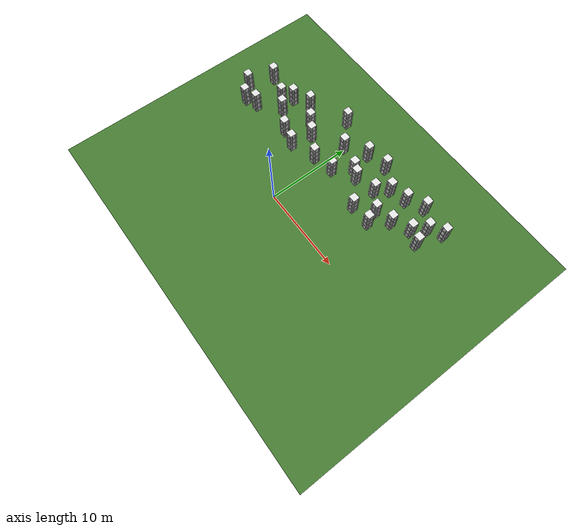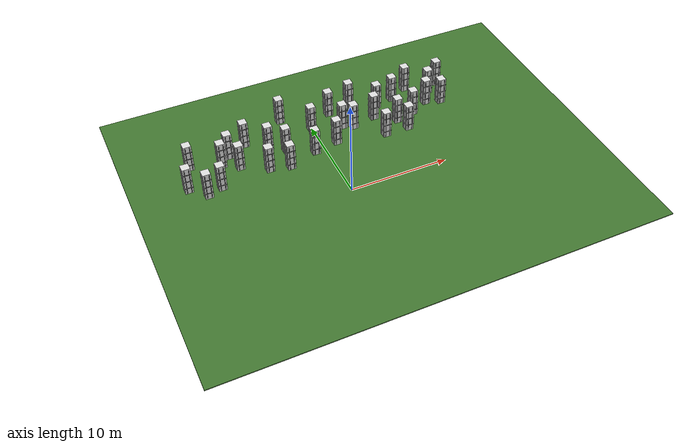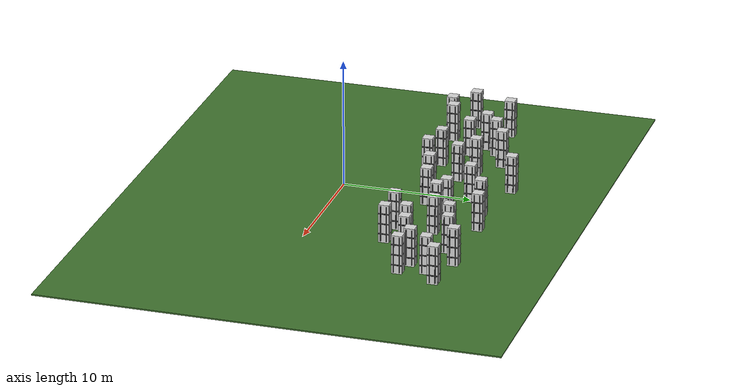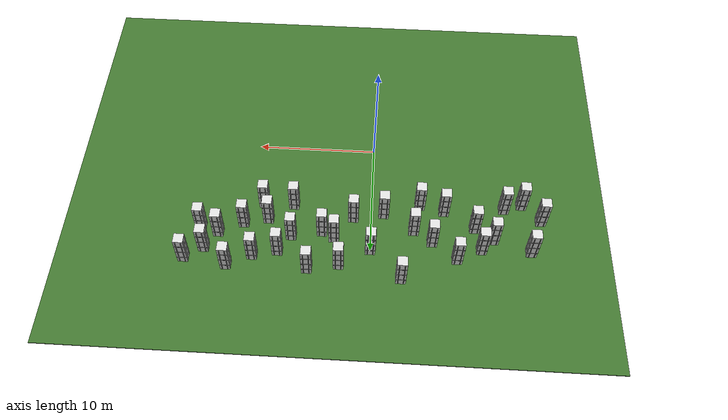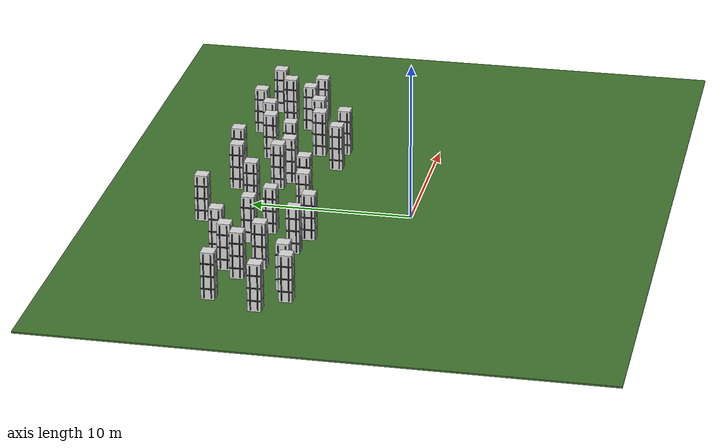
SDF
<?xml version='1.0'?>
<sdf version='1.6'>
  <world name='dense_world_complex'>

    <gui fullscreen='0'>
      <camera name='user_camera'>
        <pose>-49 27 52 0 0.75 -0.76 0</pose>
      </camera>
    </gui>

    <shadows>0</shadows>

    <light name='sun' type='directional'>
      <cast_shadows>1</cast_shadows>
      <pose>0 0 20 0 0 0</pose>
      <diffuse>0.8 0.8 0.8 1</diffuse>
      <specular>0.2 0.2 0.2 1</specular>
      <attenuation>
        <range>1000</range>
        <constant>0.9</constant>
        <linear>0.01</linear>
        <quadratic>0.001</quadratic>
      </attenuation>
      <direction>-0.5 0.1 -0.9</direction>
    </light>

    <physics name='default_physics' default='1' type='ode'>
      <max_step_size>0.005</max_step_size>
      <real_time_factor>1</real_time_factor>
      <real_time_update_rate>200</real_time_update_rate>
    </physics>

    <model name='ground'>
      <static>1</static>
      <link name='link'>
        <collision name='collision'>
          <geometry>
            <box>
              <size>45 35 0.1</size>
            </box>
          </geometry>
        </collision>
        <visual name='visual'>
          <geometry>
            <box>
              <size>45 35 0.1</size>
            </box>
          </geometry>
          <material>
            <ambient>0.25 0.45 0.18 1</ambient>
            <diffuse>0.25 0.45 0.18 1</diffuse>
          </material>
        </visual>
      </link>
      <pose>3 2 -0.05 0 0 0</pose>
    </model>

    <model name='obs_01'>
      <static>1</static>
      <pose>-14.0 6.5 1.5 0 0 0</pose>
      <link name='link'>
        <collision name='collision'>
          <geometry>
            <box>
              <size>0.8 0.8 3.0</size>
            </box>
          </geometry>
        </collision>

        <visual name='body'>
          <geometry>
            <box>
              <size>0.8 0.8 3.0</size>
            </box>
          </geometry>
          <material>
            <ambient>0.85 0.85 0.85 1</ambient>
            <diffuse>0.85 0.85 0.85 1</diffuse>
          </material>
        </visual>

        <!-- Horizontal black bands for LK corners/edges -->
        <visual name='stripe_h_1'>
          <pose>0 0 -0.8 0 0 0</pose>
          <geometry><box><size>0.84 0.84 0.10</size></box></geometry>
          <material><ambient>0.02 0.02 0.02 1</ambient><diffuse>0.02 0.02 0.02 1</diffuse></material>
        </visual>
        <visual name='stripe_h_2'>
          <pose>0 0 0.0 0 0 0</pose>
          <geometry><box><size>0.84 0.84 0.10</size></box></geometry>
          <material><ambient>0.02 0.02 0.02 1</ambient><diffuse>0.02 0.02 0.02 1</diffuse></material>
        </visual>
        <visual name='stripe_h_3'>
          <pose>0 0 0.8 0 0 0</pose>
          <geometry><box><size>0.84 0.84 0.10</size></box></geometry>
          <material><ambient>0.02 0.02 0.02 1</ambient><diffuse>0.02 0.02 0.02 1</diffuse></material>
        </visual>

        <!-- Vertical stripes on front/back direction -->
        <visual name='stripe_v_x_1'>
          <pose>-0.22 0 0 0 0 0</pose>
          <geometry><box><size>0.08 0.86 2.8</size></box></geometry>
          <material><ambient>0.02 0.02 0.02 1</ambient><diffuse>0.02 0.02 0.02 1</diffuse></material>
        </visual>
        <visual name='stripe_v_x_2'>
          <pose>0.22 0 0 0 0 0</pose>
          <geometry><box><size>0.08 0.86 2.8</size></box></geometry>
          <material><ambient>0.02 0.02 0.02 1</ambient><diffuse>0.02 0.02 0.02 1</diffuse></material>
        </visual>

        <!-- Vertical stripes on side direction -->
        <visual name='stripe_v_y_1'>
          <pose>0 -0.22 0 0 0 0</pose>
          <geometry><box><size>0.86 0.08 2.8</size></box></geometry>
          <material><ambient>0.02 0.02 0.02 1</ambient><diffuse>0.02 0.02 0.02 1</diffuse></material>
        </visual>
        <visual name='stripe_v_y_2'>
          <pose>0 0.22 0 0 0 0</pose>
          <geometry><box><size>0.86 0.08 2.8</size></box></geometry>
          <material><ambient>0.02 0.02 0.02 1</ambient><diffuse>0.02 0.02 0.02 1</diffuse></material>
        </visual>
      </link>
    </model>

    <model name='obs_02'>
      <static>1</static>
      <pose>-13.0 9.5 1.5 0 0 0</pose>
      <link name='link'>
        <collision name='collision'>
          <geometry>
            <box>
              <size>0.8 0.8 3.0</size>
            </box>
          </geometry>
        </collision>

        <visual name='body'>
          <geometry>
            <box>
              <size>0.8 0.8 3.0</size>
            </box>
          </geometry>
          <material>
            <ambient>0.85 0.85 0.85 1</ambient>
            <diffuse>0.85 0.85 0.85 1</diffuse>
          </material>
        </visual>

        <!-- Horizontal black bands for LK corners/edges -->
        <visual name='stripe_h_1'>
          <pose>0 0 -0.8 0 0 0</pose>
          <geometry><box><size>0.84 0.84 0.10</size></box></geometry>
          <material><ambient>0.02 0.02 0.02 1</ambient><diffuse>0.02 0.02 0.02 1</diffuse></material>
        </visual>
        <visual name='stripe_h_2'>
          <pose>0 0 0.0 0 0 0</pose>
          <geometry><box><size>0.84 0.84 0.10</size></box></geometry>
          <material><ambient>0.02 0.02 0.02 1</ambient><diffuse>0.02 0.02 0.02 1</diffuse></material>
        </visual>
        <visual name='stripe_h_3'>
          <pose>0 0 0.8 0 0 0</pose>
          <geometry><box><size>0.84 0.84 0.10</size></box></geometry>
          <material><ambient>0.02 0.02 0.02 1</ambient><diffuse>0.02 0.02 0.02 1</diffuse></material>
        </visual>

        <!-- Vertical stripes on front/back direction -->
        <visual name='stripe_v_x_1'>
          <pose>-0.22 0 0 0 0 0</pose>
          <geometry><box><size>0.08 0.86 2.8</size></box></geometry>
          <material><ambient>0.02 0.02 0.02 1</ambient><diffuse>0.02 0.02 0.02 1</diffuse></material>
        </visual>
        <visual name='stripe_v_x_2'>
          <pose>0.22 0 0 0 0 0</pose>
          <geometry><box><size>0.08 0.86 2.8</size></box></geometry>
          <material><ambient>0.02 0.02 0.02 1</ambient><diffuse>0.02 0.02 0.02 1</diffuse></material>
        </visual>

        <!-- Vertical stripes on side direction -->
        <visual name='stripe_v_y_1'>
          <pose>0 -0.22 0 0 0 0</pose>
          <geometry><box><size>0.86 0.08 2.8</size></box></geometry>
          <material><ambient>0.02 0.02 0.02 1</ambient><diffuse>0.02 0.02 0.02 1</diffuse></material>
        </visual>
        <visual name='stripe_v_y_2'>
          <pose>0 0.22 0 0 0 0</pose>
          <geometry><box><size>0.86 0.08 2.8</size></box></geometry>
          <material><ambient>0.02 0.02 0.02 1</ambient><diffuse>0.02 0.02 0.02 1</diffuse></material>
        </visual>
      </link>
    </model>

    <model name='obs_03'>
      <static>1</static>
      <pose>-11.0 5.5 1.5 0 0 0</pose>
      <link name='link'>
        <collision name='collision'>
          <geometry>
            <box>
              <size>0.8 0.8 3.0</size>
            </box>
          </geometry>
        </collision>

        <visual name='body'>
          <geometry>
            <box>
              <size>0.8 0.8 3.0</size>
            </box>
          </geometry>
          <material>
            <ambient>0.85 0.85 0.85 1</ambient>
            <diffuse>0.85 0.85 0.85 1</diffuse>
          </material>
        </visual>

        <!-- Horizontal black bands for LK corners/edges -->
        <visual name='stripe_h_1'>
          <pose>0 0 -0.8 0 0 0</pose>
          <geometry><box><size>0.84 0.84 0.10</size></box></geometry>
          <material><ambient>0.02 0.02 0.02 1</ambient><diffuse>0.02 0.02 0.02 1</diffuse></material>
        </visual>
        <visual name='stripe_h_2'>
          <pose>0 0 0.0 0 0 0</pose>
          <geometry><box><size>0.84 0.84 0.10</size></box></geometry>
          <material><ambient>0.02 0.02 0.02 1</ambient><diffuse>0.02 0.02 0.02 1</diffuse></material>
        </visual>
        <visual name='stripe_h_3'>
          <pose>0 0 0.8 0 0 0</pose>
          <geometry><box><size>0.84 0.84 0.10</size></box></geometry>
          <material><ambient>0.02 0.02 0.02 1</ambient><diffuse>0.02 0.02 0.02 1</diffuse></material>
        </visual>

        <!-- Vertical stripes on front/back direction -->
        <visual name='stripe_v_x_1'>
          <pose>-0.22 0 0 0 0 0</pose>
          <geometry><box><size>0.08 0.86 2.8</size></box></geometry>
          <material><ambient>0.02 0.02 0.02 1</ambient><diffuse>0.02 0.02 0.02 1</diffuse></material>
        </visual>
        <visual name='stripe_v_x_2'>
          <pose>0.22 0 0 0 0 0</pose>
          <geometry><box><size>0.08 0.86 2.8</size></box></geometry>
          <material><ambient>0.02 0.02 0.02 1</ambient><diffuse>0.02 0.02 0.02 1</diffuse></material>
        </visual>

        <!-- Vertical stripes on side direction -->
        <visual name='stripe_v_y_1'>
          <pose>0 -0.22 0 0 0 0</pose>
          <geometry><box><size>0.86 0.08 2.8</size></box></geometry>
          <material><ambient>0.02 0.02 0.02 1</ambient><diffuse>0.02 0.02 0.02 1</diffuse></material>
        </visual>
        <visual name='stripe_v_y_2'>
          <pose>0 0.22 0 0 0 0</pose>
          <geometry><box><size>0.86 0.08 2.8</size></box></geometry>
          <material><ambient>0.02 0.02 0.02 1</ambient><diffuse>0.02 0.02 0.02 1</diffuse></material>
        </visual>
      </link>
    </model>

    <model name='obs_04'>
      <static>1</static>
      <pose>-10.0 8.5 1.5 0 0 0</pose>
      <link name='link'>
        <collision name='collision'>
          <geometry>
            <box>
              <size>0.8 0.8 3.0</size>
            </box>
          </geometry>
        </collision>

        <visual name='body'>
          <geometry>
            <box>
              <size>0.8 0.8 3.0</size>
            </box>
          </geometry>
          <material>
            <ambient>0.85 0.85 0.85 1</ambient>
            <diffuse>0.85 0.85 0.85 1</diffuse>
          </material>
        </visual>

        <!-- Horizontal black bands for LK corners/edges -->
        <visual name='stripe_h_1'>
          <pose>0 0 -0.8 0 0 0</pose>
          <geometry><box><size>0.84 0.84 0.10</size></box></geometry>
          <material><ambient>0.02 0.02 0.02 1</ambient><diffuse>0.02 0.02 0.02 1</diffuse></material>
        </visual>
        <visual name='stripe_h_2'>
          <pose>0 0 0.0 0 0 0</pose>
          <geometry><box><size>0.84 0.84 0.10</size></box></geometry>
          <material><ambient>0.02 0.02 0.02 1</ambient><diffuse>0.02 0.02 0.02 1</diffuse></material>
        </visual>
        <visual name='stripe_h_3'>
          <pose>0 0 0.8 0 0 0</pose>
          <geometry><box><size>0.84 0.84 0.10</size></box></geometry>
          <material><ambient>0.02 0.02 0.02 1</ambient><diffuse>0.02 0.02 0.02 1</diffuse></material>
        </visual>

        <!-- Vertical stripes on front/back direction -->
        <visual name='stripe_v_x_1'>
          <pose>-0.22 0 0 0 0 0</pose>
          <geometry><box><size>0.08 0.86 2.8</size></box></geometry>
          <material><ambient>0.02 0.02 0.02 1</ambient><diffuse>0.02 0.02 0.02 1</diffuse></material>
        </visual>
        <visual name='stripe_v_x_2'>
          <pose>0.22 0 0 0 0 0</pose>
          <geometry><box><size>0.08 0.86 2.8</size></box></geometry>
          <material><ambient>0.02 0.02 0.02 1</ambient><diffuse>0.02 0.02 0.02 1</diffuse></material>
        </visual>

        <!-- Vertical stripes on side direction -->
        <visual name='stripe_v_y_1'>
          <pose>0 -0.22 0 0 0 0</pose>
          <geometry><box><size>0.86 0.08 2.8</size></box></geometry>
          <material><ambient>0.02 0.02 0.02 1</ambient><diffuse>0.02 0.02 0.02 1</diffuse></material>
        </visual>
        <visual name='stripe_v_y_2'>
          <pose>0 0.22 0 0 0 0</pose>
          <geometry><box><size>0.86 0.08 2.8</size></box></geometry>
          <material><ambient>0.02 0.02 0.02 1</ambient><diffuse>0.02 0.02 0.02 1</diffuse></material>
        </visual>
      </link>
    </model>

    <model name='obs_05'>
      <static>1</static>
      <pose>-8.5 7.5 1.5 0 0 0</pose>
      <link name='link'>
        <collision name='collision'>
          <geometry>
            <box>
              <size>0.8 0.8 3.0</size>
            </box>
          </geometry>
        </collision>

        <visual name='body'>
          <geometry>
            <box>
              <size>0.8 0.8 3.0</size>
            </box>
          </geometry>
          <material>
            <ambient>0.85 0.85 0.85 1</ambient>
            <diffuse>0.85 0.85 0.85 1</diffuse>
          </material>
        </visual>

        <!-- Horizontal black bands for LK corners/edges -->
        <visual name='stripe_h_1'>
          <pose>0 0 -0.8 0 0 0</pose>
          <geometry><box><size>0.84 0.84 0.10</size></box></geometry>
          <material><ambient>0.02 0.02 0.02 1</ambient><diffuse>0.02 0.02 0.02 1</diffuse></material>
        </visual>
        <visual name='stripe_h_2'>
          <pose>0 0 0.0 0 0 0</pose>
          <geometry><box><size>0.84 0.84 0.10</size></box></geometry>
          <material><ambient>0.02 0.02 0.02 1</ambient><diffuse>0.02 0.02 0.02 1</diffuse></material>
        </visual>
        <visual name='stripe_h_3'>
          <pose>0 0 0.8 0 0 0</pose>
          <geometry><box><size>0.84 0.84 0.10</size></box></geometry>
          <material><ambient>0.02 0.02 0.02 1</ambient><diffuse>0.02 0.02 0.02 1</diffuse></material>
        </visual>

        <!-- Vertical stripes on front/back direction -->
        <visual name='stripe_v_x_1'>
          <pose>-0.22 0 0 0 0 0</pose>
          <geometry><box><size>0.08 0.86 2.8</size></box></geometry>
          <material><ambient>0.02 0.02 0.02 1</ambient><diffuse>0.02 0.02 0.02 1</diffuse></material>
        </visual>
        <visual name='stripe_v_x_2'>
          <pose>0.22 0 0 0 0 0</pose>
          <geometry><box><size>0.08 0.86 2.8</size></box></geometry>
          <material><ambient>0.02 0.02 0.02 1</ambient><diffuse>0.02 0.02 0.02 1</diffuse></material>
        </visual>

        <!-- Vertical stripes on side direction -->
        <visual name='stripe_v_y_1'>
          <pose>0 -0.22 0 0 0 0</pose>
          <geometry><box><size>0.86 0.08 2.8</size></box></geometry>
          <material><ambient>0.02 0.02 0.02 1</ambient><diffuse>0.02 0.02 0.02 1</diffuse></material>
        </visual>
        <visual name='stripe_v_y_2'>
          <pose>0 0.22 0 0 0 0</pose>
          <geometry><box><size>0.86 0.08 2.8</size></box></geometry>
          <material><ambient>0.02 0.02 0.02 1</ambient><diffuse>0.02 0.02 0.02 1</diffuse></material>
        </visual>
      </link>
    </model>

    <model name='obs_06'>
      <static>1</static>
      <pose>-7.0 10.5 1.5 0 0 0</pose>
      <link name='link'>
        <collision name='collision'>
          <geometry>
            <box>
              <size>0.8 0.8 3.0</size>
            </box>
          </geometry>
        </collision>

        <visual name='body'>
          <geometry>
            <box>
              <size>0.8 0.8 3.0</size>
            </box>
          </geometry>
          <material>
            <ambient>0.85 0.85 0.85 1</ambient>
            <diffuse>0.85 0.85 0.85 1</diffuse>
          </material>
        </visual>

        <!-- Horizontal black bands for LK corners/edges -->
        <visual name='stripe_h_1'>
          <pose>0 0 -0.8 0 0 0</pose>
          <geometry><box><size>0.84 0.84 0.10</size></box></geometry>
          <material><ambient>0.02 0.02 0.02 1</ambient><diffuse>0.02 0.02 0.02 1</diffuse></material>
        </visual>
        <visual name='stripe_h_2'>
          <pose>0 0 0.0 0 0 0</pose>
          <geometry><box><size>0.84 0.84 0.10</size></box></geometry>
          <material><ambient>0.02 0.02 0.02 1</ambient><diffuse>0.02 0.02 0.02 1</diffuse></material>
        </visual>
        <visual name='stripe_h_3'>
          <pose>0 0 0.8 0 0 0</pose>
          <geometry><box><size>0.84 0.84 0.10</size></box></geometry>
          <material><ambient>0.02 0.02 0.02 1</ambient><diffuse>0.02 0.02 0.02 1</diffuse></material>
        </visual>

        <!-- Vertical stripes on front/back direction -->
        <visual name='stripe_v_x_1'>
          <pose>-0.22 0 0 0 0 0</pose>
          <geometry><box><size>0.08 0.86 2.8</size></box></geometry>
          <material><ambient>0.02 0.02 0.02 1</ambient><diffuse>0.02 0.02 0.02 1</diffuse></material>
        </visual>
        <visual name='stripe_v_x_2'>
          <pose>0.22 0 0 0 0 0</pose>
          <geometry><box><size>0.08 0.86 2.8</size></box></geometry>
          <material><ambient>0.02 0.02 0.02 1</ambient><diffuse>0.02 0.02 0.02 1</diffuse></material>
        </visual>

        <!-- Vertical stripes on side direction -->
        <visual name='stripe_v_y_1'>
          <pose>0 -0.22 0 0 0 0</pose>
          <geometry><box><size>0.86 0.08 2.8</size></box></geometry>
          <material><ambient>0.02 0.02 0.02 1</ambient><diffuse>0.02 0.02 0.02 1</diffuse></material>
        </visual>
        <visual name='stripe_v_y_2'>
          <pose>0 0.22 0 0 0 0</pose>
          <geometry><box><size>0.86 0.08 2.8</size></box></geometry>
          <material><ambient>0.02 0.02 0.02 1</ambient><diffuse>0.02 0.02 0.02 1</diffuse></material>
        </visual>
      </link>
    </model>

    <model name='obs_07'>
      <static>1</static>
      <pose>-6.0 6.0 1.5 0 0 0</pose>
      <link name='link'>
        <collision name='collision'>
          <geometry>
            <box>
              <size>0.8 0.8 3.0</size>
            </box>
          </geometry>
        </collision>

        <visual name='body'>
          <geometry>
            <box>
              <size>0.8 0.8 3.0</size>
            </box>
          </geometry>
          <material>
            <ambient>0.85 0.85 0.85 1</ambient>
            <diffuse>0.85 0.85 0.85 1</diffuse>
          </material>
        </visual>

        <!-- Horizontal black bands for LK corners/edges -->
        <visual name='stripe_h_1'>
          <pose>0 0 -0.8 0 0 0</pose>
          <geometry><box><size>0.84 0.84 0.10</size></box></geometry>
          <material><ambient>0.02 0.02 0.02 1</ambient><diffuse>0.02 0.02 0.02 1</diffuse></material>
        </visual>
        <visual name='stripe_h_2'>
          <pose>0 0 0.0 0 0 0</pose>
          <geometry><box><size>0.84 0.84 0.10</size></box></geometry>
          <material><ambient>0.02 0.02 0.02 1</ambient><diffuse>0.02 0.02 0.02 1</diffuse></material>
        </visual>
        <visual name='stripe_h_3'>
          <pose>0 0 0.8 0 0 0</pose>
          <geometry><box><size>0.84 0.84 0.10</size></box></geometry>
          <material><ambient>0.02 0.02 0.02 1</ambient><diffuse>0.02 0.02 0.02 1</diffuse></material>
        </visual>

        <!-- Vertical stripes on front/back direction -->
        <visual name='stripe_v_x_1'>
          <pose>-0.22 0 0 0 0 0</pose>
          <geometry><box><size>0.08 0.86 2.8</size></box></geometry>
          <material><ambient>0.02 0.02 0.02 1</ambient><diffuse>0.02 0.02 0.02 1</diffuse></material>
        </visual>
        <visual name='stripe_v_x_2'>
          <pose>0.22 0 0 0 0 0</pose>
          <geometry><box><size>0.08 0.86 2.8</size></box></geometry>
          <material><ambient>0.02 0.02 0.02 1</ambient><diffuse>0.02 0.02 0.02 1</diffuse></material>
        </visual>

        <!-- Vertical stripes on side direction -->
        <visual name='stripe_v_y_1'>
          <pose>0 -0.22 0 0 0 0</pose>
          <geometry><box><size>0.86 0.08 2.8</size></box></geometry>
          <material><ambient>0.02 0.02 0.02 1</ambient><diffuse>0.02 0.02 0.02 1</diffuse></material>
        </visual>
        <visual name='stripe_v_y_2'>
          <pose>0 0.22 0 0 0 0</pose>
          <geometry><box><size>0.86 0.08 2.8</size></box></geometry>
          <material><ambient>0.02 0.02 0.02 1</ambient><diffuse>0.02 0.02 0.02 1</diffuse></material>
        </visual>
      </link>
    </model>

    <model name='obs_08'>
      <static>1</static>
      <pose>-5.0 9.0 1.5 0 0 0</pose>
      <link name='link'>
        <collision name='collision'>
          <geometry>
            <box>
              <size>0.8 0.8 3.0</size>
            </box>
          </geometry>
        </collision>

        <visual name='body'>
          <geometry>
            <box>
              <size>0.8 0.8 3.0</size>
            </box>
          </geometry>
          <material>
            <ambient>0.85 0.85 0.85 1</ambient>
            <diffuse>0.85 0.85 0.85 1</diffuse>
          </material>
        </visual>

        <!-- Horizontal black bands for LK corners/edges -->
        <visual name='stripe_h_1'>
          <pose>0 0 -0.8 0 0 0</pose>
          <geometry><box><size>0.84 0.84 0.10</size></box></geometry>
          <material><ambient>0.02 0.02 0.02 1</ambient><diffuse>0.02 0.02 0.02 1</diffuse></material>
        </visual>
        <visual name='stripe_h_2'>
          <pose>0 0 0.0 0 0 0</pose>
          <geometry><box><size>0.84 0.84 0.10</size></box></geometry>
          <material><ambient>0.02 0.02 0.02 1</ambient><diffuse>0.02 0.02 0.02 1</diffuse></material>
        </visual>
        <visual name='stripe_h_3'>
          <pose>0 0 0.8 0 0 0</pose>
          <geometry><box><size>0.84 0.84 0.10</size></box></geometry>
          <material><ambient>0.02 0.02 0.02 1</ambient><diffuse>0.02 0.02 0.02 1</diffuse></material>
        </visual>

        <!-- Vertical stripes on front/back direction -->
        <visual name='stripe_v_x_1'>
          <pose>-0.22 0 0 0 0 0</pose>
          <geometry><box><size>0.08 0.86 2.8</size></box></geometry>
          <material><ambient>0.02 0.02 0.02 1</ambient><diffuse>0.02 0.02 0.02 1</diffuse></material>
        </visual>
        <visual name='stripe_v_x_2'>
          <pose>0.22 0 0 0 0 0</pose>
          <geometry><box><size>0.08 0.86 2.8</size></box></geometry>
          <material><ambient>0.02 0.02 0.02 1</ambient><diffuse>0.02 0.02 0.02 1</diffuse></material>
        </visual>

        <!-- Vertical stripes on side direction -->
        <visual name='stripe_v_y_1'>
          <pose>0 -0.22 0 0 0 0</pose>
          <geometry><box><size>0.86 0.08 2.8</size></box></geometry>
          <material><ambient>0.02 0.02 0.02 1</ambient><diffuse>0.02 0.02 0.02 1</diffuse></material>
        </visual>
        <visual name='stripe_v_y_2'>
          <pose>0 0.22 0 0 0 0</pose>
          <geometry><box><size>0.86 0.08 2.8</size></box></geometry>
          <material><ambient>0.02 0.02 0.02 1</ambient><diffuse>0.02 0.02 0.02 1</diffuse></material>
        </visual>
      </link>
    </model>

    <model name='obs_09'>
      <static>1</static>
      <pose>-3.5 8.0 1.5 0 0 0</pose>
      <link name='link'>
        <collision name='collision'>
          <geometry>
            <box>
              <size>0.8 0.8 3.0</size>
            </box>
          </geometry>
        </collision>

        <visual name='body'>
          <geometry>
            <box>
              <size>0.8 0.8 3.0</size>
            </box>
          </geometry>
          <material>
            <ambient>0.85 0.85 0.85 1</ambient>
            <diffuse>0.85 0.85 0.85 1</diffuse>
          </material>
        </visual>

        <!-- Horizontal black bands for LK corners/edges -->
        <visual name='stripe_h_1'>
          <pose>0 0 -0.8 0 0 0</pose>
          <geometry><box><size>0.84 0.84 0.10</size></box></geometry>
          <material><ambient>0.02 0.02 0.02 1</ambient><diffuse>0.02 0.02 0.02 1</diffuse></material>
        </visual>
        <visual name='stripe_h_2'>
          <pose>0 0 0.0 0 0 0</pose>
          <geometry><box><size>0.84 0.84 0.10</size></box></geometry>
          <material><ambient>0.02 0.02 0.02 1</ambient><diffuse>0.02 0.02 0.02 1</diffuse></material>
        </visual>
        <visual name='stripe_h_3'>
          <pose>0 0 0.8 0 0 0</pose>
          <geometry><box><size>0.84 0.84 0.10</size></box></geometry>
          <material><ambient>0.02 0.02 0.02 1</ambient><diffuse>0.02 0.02 0.02 1</diffuse></material>
        </visual>

        <!-- Vertical stripes on front/back direction -->
        <visual name='stripe_v_x_1'>
          <pose>-0.22 0 0 0 0 0</pose>
          <geometry><box><size>0.08 0.86 2.8</size></box></geometry>
          <material><ambient>0.02 0.02 0.02 1</ambient><diffuse>0.02 0.02 0.02 1</diffuse></material>
        </visual>
        <visual name='stripe_v_x_2'>
          <pose>0.22 0 0 0 0 0</pose>
          <geometry><box><size>0.08 0.86 2.8</size></box></geometry>
          <material><ambient>0.02 0.02 0.02 1</ambient><diffuse>0.02 0.02 0.02 1</diffuse></material>
        </visual>

        <!-- Vertical stripes on side direction -->
        <visual name='stripe_v_y_1'>
          <pose>0 -0.22 0 0 0 0</pose>
          <geometry><box><size>0.86 0.08 2.8</size></box></geometry>
          <material><ambient>0.02 0.02 0.02 1</ambient><diffuse>0.02 0.02 0.02 1</diffuse></material>
        </visual>
        <visual name='stripe_v_y_2'>
          <pose>0 0.22 0 0 0 0</pose>
          <geometry><box><size>0.86 0.08 2.8</size></box></geometry>
          <material><ambient>0.02 0.02 0.02 1</ambient><diffuse>0.02 0.02 0.02 1</diffuse></material>
        </visual>
      </link>
    </model>

    <model name='obs_10'>
      <static>1</static>
      <pose>-2.5 12.5 1.5 0 0 0</pose>
      <link name='link'>
        <collision name='collision'>
          <geometry>
            <box>
              <size>0.8 0.8 3.0</size>
            </box>
          </geometry>
        </collision>

        <visual name='body'>
          <geometry>
            <box>
              <size>0.8 0.8 3.0</size>
            </box>
          </geometry>
          <material>
            <ambient>0.85 0.85 0.85 1</ambient>
            <diffuse>0.85 0.85 0.85 1</diffuse>
          </material>
        </visual>

        <!-- Horizontal black bands for LK corners/edges -->
        <visual name='stripe_h_1'>
          <pose>0 0 -0.8 0 0 0</pose>
          <geometry><box><size>0.84 0.84 0.10</size></box></geometry>
          <material><ambient>0.02 0.02 0.02 1</ambient><diffuse>0.02 0.02 0.02 1</diffuse></material>
        </visual>
        <visual name='stripe_h_2'>
          <pose>0 0 0.0 0 0 0</pose>
          <geometry><box><size>0.84 0.84 0.10</size></box></geometry>
          <material><ambient>0.02 0.02 0.02 1</ambient><diffuse>0.02 0.02 0.02 1</diffuse></material>
        </visual>
        <visual name='stripe_h_3'>
          <pose>0 0 0.8 0 0 0</pose>
          <geometry><box><size>0.84 0.84 0.10</size></box></geometry>
          <material><ambient>0.02 0.02 0.02 1</ambient><diffuse>0.02 0.02 0.02 1</diffuse></material>
        </visual>

        <!-- Vertical stripes on front/back direction -->
        <visual name='stripe_v_x_1'>
          <pose>-0.22 0 0 0 0 0</pose>
          <geometry><box><size>0.08 0.86 2.8</size></box></geometry>
          <material><ambient>0.02 0.02 0.02 1</ambient><diffuse>0.02 0.02 0.02 1</diffuse></material>
        </visual>
        <visual name='stripe_v_x_2'>
          <pose>0.22 0 0 0 0 0</pose>
          <geometry><box><size>0.08 0.86 2.8</size></box></geometry>
          <material><ambient>0.02 0.02 0.02 1</ambient><diffuse>0.02 0.02 0.02 1</diffuse></material>
        </visual>

        <!-- Vertical stripes on side direction -->
        <visual name='stripe_v_y_1'>
          <pose>0 -0.22 0 0 0 0</pose>
          <geometry><box><size>0.86 0.08 2.8</size></box></geometry>
          <material><ambient>0.02 0.02 0.02 1</ambient><diffuse>0.02 0.02 0.02 1</diffuse></material>
        </visual>
        <visual name='stripe_v_y_2'>
          <pose>0 0.22 0 0 0 0</pose>
          <geometry><box><size>0.86 0.08 2.8</size></box></geometry>
          <material><ambient>0.02 0.02 0.02 1</ambient><diffuse>0.02 0.02 0.02 1</diffuse></material>
        </visual>
      </link>
    </model>

    <model name='obs_11'>
      <static>1</static>
      <pose>-1.0 6.5 1.5 0 0 0</pose>
      <link name='link'>
        <collision name='collision'>
          <geometry>
            <box>
              <size>0.8 0.8 3.0</size>
            </box>
          </geometry>
        </collision>

        <visual name='body'>
          <geometry>
            <box>
              <size>0.8 0.8 3.0</size>
            </box>
          </geometry>
          <material>
            <ambient>0.85 0.85 0.85 1</ambient>
            <diffuse>0.85 0.85 0.85 1</diffuse>
          </material>
        </visual>

        <!-- Horizontal black bands for LK corners/edges -->
        <visual name='stripe_h_1'>
          <pose>0 0 -0.8 0 0 0</pose>
          <geometry><box><size>0.84 0.84 0.10</size></box></geometry>
          <material><ambient>0.02 0.02 0.02 1</ambient><diffuse>0.02 0.02 0.02 1</diffuse></material>
        </visual>
        <visual name='stripe_h_2'>
          <pose>0 0 0.0 0 0 0</pose>
          <geometry><box><size>0.84 0.84 0.10</size></box></geometry>
          <material><ambient>0.02 0.02 0.02 1</ambient><diffuse>0.02 0.02 0.02 1</diffuse></material>
        </visual>
        <visual name='stripe_h_3'>
          <pose>0 0 0.8 0 0 0</pose>
          <geometry><box><size>0.84 0.84 0.10</size></box></geometry>
          <material><ambient>0.02 0.02 0.02 1</ambient><diffuse>0.02 0.02 0.02 1</diffuse></material>
        </visual>

        <!-- Vertical stripes on front/back direction -->
        <visual name='stripe_v_x_1'>
          <pose>-0.22 0 0 0 0 0</pose>
          <geometry><box><size>0.08 0.86 2.8</size></box></geometry>
          <material><ambient>0.02 0.02 0.02 1</ambient><diffuse>0.02 0.02 0.02 1</diffuse></material>
        </visual>
        <visual name='stripe_v_x_2'>
          <pose>0.22 0 0 0 0 0</pose>
          <geometry><box><size>0.08 0.86 2.8</size></box></geometry>
          <material><ambient>0.02 0.02 0.02 1</ambient><diffuse>0.02 0.02 0.02 1</diffuse></material>
        </visual>

        <!-- Vertical stripes on side direction -->
        <visual name='stripe_v_y_1'>
          <pose>0 -0.22 0 0 0 0</pose>
          <geometry><box><size>0.86 0.08 2.8</size></box></geometry>
          <material><ambient>0.02 0.02 0.02 1</ambient><diffuse>0.02 0.02 0.02 1</diffuse></material>
        </visual>
        <visual name='stripe_v_y_2'>
          <pose>0 0.22 0 0 0 0</pose>
          <geometry><box><size>0.86 0.08 2.8</size></box></geometry>
          <material><ambient>0.02 0.02 0.02 1</ambient><diffuse>0.02 0.02 0.02 1</diffuse></material>
        </visual>
      </link>
    </model>

    <model name='obs_12'>
      <static>1</static>
      <pose>0.0 10.0 1.5 0 0 0</pose>
      <link name='link'>
        <collision name='collision'>
          <geometry>
            <box>
              <size>0.8 0.8 3.0</size>
            </box>
          </geometry>
        </collision>

        <visual name='body'>
          <geometry>
            <box>
              <size>0.8 0.8 3.0</size>
            </box>
          </geometry>
          <material>
            <ambient>0.85 0.85 0.85 1</ambient>
            <diffuse>0.85 0.85 0.85 1</diffuse>
          </material>
        </visual>

        <!-- Horizontal black bands for LK corners/edges -->
        <visual name='stripe_h_1'>
          <pose>0 0 -0.8 0 0 0</pose>
          <geometry><box><size>0.84 0.84 0.10</size></box></geometry>
          <material><ambient>0.02 0.02 0.02 1</ambient><diffuse>0.02 0.02 0.02 1</diffuse></material>
        </visual>
        <visual name='stripe_h_2'>
          <pose>0 0 0.0 0 0 0</pose>
          <geometry><box><size>0.84 0.84 0.10</size></box></geometry>
          <material><ambient>0.02 0.02 0.02 1</ambient><diffuse>0.02 0.02 0.02 1</diffuse></material>
        </visual>
        <visual name='stripe_h_3'>
          <pose>0 0 0.8 0 0 0</pose>
          <geometry><box><size>0.84 0.84 0.10</size></box></geometry>
          <material><ambient>0.02 0.02 0.02 1</ambient><diffuse>0.02 0.02 0.02 1</diffuse></material>
        </visual>

        <!-- Vertical stripes on front/back direction -->
        <visual name='stripe_v_x_1'>
          <pose>-0.22 0 0 0 0 0</pose>
          <geometry><box><size>0.08 0.86 2.8</size></box></geometry>
          <material><ambient>0.02 0.02 0.02 1</ambient><diffuse>0.02 0.02 0.02 1</diffuse></material>
        </visual>
        <visual name='stripe_v_x_2'>
          <pose>0.22 0 0 0 0 0</pose>
          <geometry><box><size>0.08 0.86 2.8</size></box></geometry>
          <material><ambient>0.02 0.02 0.02 1</ambient><diffuse>0.02 0.02 0.02 1</diffuse></material>
        </visual>

        <!-- Vertical stripes on side direction -->
        <visual name='stripe_v_y_1'>
          <pose>0 -0.22 0 0 0 0</pose>
          <geometry><box><size>0.86 0.08 2.8</size></box></geometry>
          <material><ambient>0.02 0.02 0.02 1</ambient><diffuse>0.02 0.02 0.02 1</diffuse></material>
        </visual>
        <visual name='stripe_v_y_2'>
          <pose>0 0.22 0 0 0 0</pose>
          <geometry><box><size>0.86 0.08 2.8</size></box></geometry>
          <material><ambient>0.02 0.02 0.02 1</ambient><diffuse>0.02 0.02 0.02 1</diffuse></material>
        </visual>
      </link>
    </model>

    <model name='obs_13'>
      <static>1</static>
      <pose>1.5 7.0 1.5 0 0 0</pose>
      <link name='link'>
        <collision name='collision'>
          <geometry>
            <box>
              <size>0.8 0.8 3.0</size>
            </box>
          </geometry>
        </collision>

        <visual name='body'>
          <geometry>
            <box>
              <size>0.8 0.8 3.0</size>
            </box>
          </geometry>
          <material>
            <ambient>0.85 0.85 0.85 1</ambient>
            <diffuse>0.85 0.85 0.85 1</diffuse>
          </material>
        </visual>

        <!-- Horizontal black bands for LK corners/edges -->
        <visual name='stripe_h_1'>
          <pose>0 0 -0.8 0 0 0</pose>
          <geometry><box><size>0.84 0.84 0.10</size></box></geometry>
          <material><ambient>0.02 0.02 0.02 1</ambient><diffuse>0.02 0.02 0.02 1</diffuse></material>
        </visual>
        <visual name='stripe_h_2'>
          <pose>0 0 0.0 0 0 0</pose>
          <geometry><box><size>0.84 0.84 0.10</size></box></geometry>
          <material><ambient>0.02 0.02 0.02 1</ambient><diffuse>0.02 0.02 0.02 1</diffuse></material>
        </visual>
        <visual name='stripe_h_3'>
          <pose>0 0 0.8 0 0 0</pose>
          <geometry><box><size>0.84 0.84 0.10</size></box></geometry>
          <material><ambient>0.02 0.02 0.02 1</ambient><diffuse>0.02 0.02 0.02 1</diffuse></material>
        </visual>

        <!-- Vertical stripes on front/back direction -->
        <visual name='stripe_v_x_1'>
          <pose>-0.22 0 0 0 0 0</pose>
          <geometry><box><size>0.08 0.86 2.8</size></box></geometry>
          <material><ambient>0.02 0.02 0.02 1</ambient><diffuse>0.02 0.02 0.02 1</diffuse></material>
        </visual>
        <visual name='stripe_v_x_2'>
          <pose>0.22 0 0 0 0 0</pose>
          <geometry><box><size>0.08 0.86 2.8</size></box></geometry>
          <material><ambient>0.02 0.02 0.02 1</ambient><diffuse>0.02 0.02 0.02 1</diffuse></material>
        </visual>

        <!-- Vertical stripes on side direction -->
        <visual name='stripe_v_y_1'>
          <pose>0 -0.22 0 0 0 0</pose>
          <geometry><box><size>0.86 0.08 2.8</size></box></geometry>
          <material><ambient>0.02 0.02 0.02 1</ambient><diffuse>0.02 0.02 0.02 1</diffuse></material>
        </visual>
        <visual name='stripe_v_y_2'>
          <pose>0 0.22 0 0 0 0</pose>
          <geometry><box><size>0.86 0.08 2.8</size></box></geometry>
          <material><ambient>0.02 0.02 0.02 1</ambient><diffuse>0.02 0.02 0.02 1</diffuse></material>
        </visual>
      </link>
    </model>

    <model name='obs_14'>
      <static>1</static>
      <pose>2.5 11.5 1.5 0 0 0</pose>
      <link name='link'>
        <collision name='collision'>
          <geometry>
            <box>
              <size>0.8 0.8 3.0</size>
            </box>
          </geometry>
        </collision>

        <visual name='body'>
          <geometry>
            <box>
              <size>0.8 0.8 3.0</size>
            </box>
          </geometry>
          <material>
            <ambient>0.85 0.85 0.85 1</ambient>
            <diffuse>0.85 0.85 0.85 1</diffuse>
          </material>
        </visual>

        <!-- Horizontal black bands for LK corners/edges -->
        <visual name='stripe_h_1'>
          <pose>0 0 -0.8 0 0 0</pose>
          <geometry><box><size>0.84 0.84 0.10</size></box></geometry>
          <material><ambient>0.02 0.02 0.02 1</ambient><diffuse>0.02 0.02 0.02 1</diffuse></material>
        </visual>
        <visual name='stripe_h_2'>
          <pose>0 0 0.0 0 0 0</pose>
          <geometry><box><size>0.84 0.84 0.10</size></box></geometry>
          <material><ambient>0.02 0.02 0.02 1</ambient><diffuse>0.02 0.02 0.02 1</diffuse></material>
        </visual>
        <visual name='stripe_h_3'>
          <pose>0 0 0.8 0 0 0</pose>
          <geometry><box><size>0.84 0.84 0.10</size></box></geometry>
          <material><ambient>0.02 0.02 0.02 1</ambient><diffuse>0.02 0.02 0.02 1</diffuse></material>
        </visual>

        <!-- Vertical stripes on front/back direction -->
        <visual name='stripe_v_x_1'>
          <pose>-0.22 0 0 0 0 0</pose>
          <geometry><box><size>0.08 0.86 2.8</size></box></geometry>
          <material><ambient>0.02 0.02 0.02 1</ambient><diffuse>0.02 0.02 0.02 1</diffuse></material>
        </visual>
        <visual name='stripe_v_x_2'>
          <pose>0.22 0 0 0 0 0</pose>
          <geometry><box><size>0.08 0.86 2.8</size></box></geometry>
          <material><ambient>0.02 0.02 0.02 1</ambient><diffuse>0.02 0.02 0.02 1</diffuse></material>
        </visual>

        <!-- Vertical stripes on side direction -->
        <visual name='stripe_v_y_1'>
          <pose>0 -0.22 0 0 0 0</pose>
          <geometry><box><size>0.86 0.08 2.8</size></box></geometry>
          <material><ambient>0.02 0.02 0.02 1</ambient><diffuse>0.02 0.02 0.02 1</diffuse></material>
        </visual>
        <visual name='stripe_v_y_2'>
          <pose>0 0.22 0 0 0 0</pose>
          <geometry><box><size>0.86 0.08 2.8</size></box></geometry>
          <material><ambient>0.02 0.02 0.02 1</ambient><diffuse>0.02 0.02 0.02 1</diffuse></material>
        </visual>
      </link>
    </model>

    <model name='obs_15'>
      <static>1</static>
      <pose>4.0 8.5 1.5 0 0 0</pose>
      <link name='link'>
        <collision name='collision'>
          <geometry>
            <box>
              <size>0.8 0.8 3.0</size>
            </box>
          </geometry>
        </collision>

        <visual name='body'>
          <geometry>
            <box>
              <size>0.8 0.8 3.0</size>
            </box>
          </geometry>
          <material>
            <ambient>0.85 0.85 0.85 1</ambient>
            <diffuse>0.85 0.85 0.85 1</diffuse>
          </material>
        </visual>

        <!-- Horizontal black bands for LK corners/edges -->
        <visual name='stripe_h_1'>
          <pose>0 0 -0.8 0 0 0</pose>
          <geometry><box><size>0.84 0.84 0.10</size></box></geometry>
          <material><ambient>0.02 0.02 0.02 1</ambient><diffuse>0.02 0.02 0.02 1</diffuse></material>
        </visual>
        <visual name='stripe_h_2'>
          <pose>0 0 0.0 0 0 0</pose>
          <geometry><box><size>0.84 0.84 0.10</size></box></geometry>
          <material><ambient>0.02 0.02 0.02 1</ambient><diffuse>0.02 0.02 0.02 1</diffuse></material>
        </visual>
        <visual name='stripe_h_3'>
          <pose>0 0 0.8 0 0 0</pose>
          <geometry><box><size>0.84 0.84 0.10</size></box></geometry>
          <material><ambient>0.02 0.02 0.02 1</ambient><diffuse>0.02 0.02 0.02 1</diffuse></material>
        </visual>

        <!-- Vertical stripes on front/back direction -->
        <visual name='stripe_v_x_1'>
          <pose>-0.22 0 0 0 0 0</pose>
          <geometry><box><size>0.08 0.86 2.8</size></box></geometry>
          <material><ambient>0.02 0.02 0.02 1</ambient><diffuse>0.02 0.02 0.02 1</diffuse></material>
        </visual>
        <visual name='stripe_v_x_2'>
          <pose>0.22 0 0 0 0 0</pose>
          <geometry><box><size>0.08 0.86 2.8</size></box></geometry>
          <material><ambient>0.02 0.02 0.02 1</ambient><diffuse>0.02 0.02 0.02 1</diffuse></material>
        </visual>

        <!-- Vertical stripes on side direction -->
        <visual name='stripe_v_y_1'>
          <pose>0 -0.22 0 0 0 0</pose>
          <geometry><box><size>0.86 0.08 2.8</size></box></geometry>
          <material><ambient>0.02 0.02 0.02 1</ambient><diffuse>0.02 0.02 0.02 1</diffuse></material>
        </visual>
        <visual name='stripe_v_y_2'>
          <pose>0 0.22 0 0 0 0</pose>
          <geometry><box><size>0.86 0.08 2.8</size></box></geometry>
          <material><ambient>0.02 0.02 0.02 1</ambient><diffuse>0.02 0.02 0.02 1</diffuse></material>
        </visual>
      </link>
    </model>

    <model name='obs_16'>
      <static>1</static>
      <pose>5.0 12.0 1.5 0 0 0</pose>
      <link name='link'>
        <collision name='collision'>
          <geometry>
            <box>
              <size>0.8 0.8 3.0</size>
            </box>
          </geometry>
        </collision>

        <visual name='body'>
          <geometry>
            <box>
              <size>0.8 0.8 3.0</size>
            </box>
          </geometry>
          <material>
            <ambient>0.85 0.85 0.85 1</ambient>
            <diffuse>0.85 0.85 0.85 1</diffuse>
          </material>
        </visual>

        <!-- Horizontal black bands for LK corners/edges -->
        <visual name='stripe_h_1'>
          <pose>0 0 -0.8 0 0 0</pose>
          <geometry><box><size>0.84 0.84 0.10</size></box></geometry>
          <material><ambient>0.02 0.02 0.02 1</ambient><diffuse>0.02 0.02 0.02 1</diffuse></material>
        </visual>
        <visual name='stripe_h_2'>
          <pose>0 0 0.0 0 0 0</pose>
          <geometry><box><size>0.84 0.84 0.10</size></box></geometry>
          <material><ambient>0.02 0.02 0.02 1</ambient><diffuse>0.02 0.02 0.02 1</diffuse></material>
        </visual>
        <visual name='stripe_h_3'>
          <pose>0 0 0.8 0 0 0</pose>
          <geometry><box><size>0.84 0.84 0.10</size></box></geometry>
          <material><ambient>0.02 0.02 0.02 1</ambient><diffuse>0.02 0.02 0.02 1</diffuse></material>
        </visual>

        <!-- Vertical stripes on front/back direction -->
        <visual name='stripe_v_x_1'>
          <pose>-0.22 0 0 0 0 0</pose>
          <geometry><box><size>0.08 0.86 2.8</size></box></geometry>
          <material><ambient>0.02 0.02 0.02 1</ambient><diffuse>0.02 0.02 0.02 1</diffuse></material>
        </visual>
        <visual name='stripe_v_x_2'>
          <pose>0.22 0 0 0 0 0</pose>
          <geometry><box><size>0.08 0.86 2.8</size></box></geometry>
          <material><ambient>0.02 0.02 0.02 1</ambient><diffuse>0.02 0.02 0.02 1</diffuse></material>
        </visual>

        <!-- Vertical stripes on side direction -->
        <visual name='stripe_v_y_1'>
          <pose>0 -0.22 0 0 0 0</pose>
          <geometry><box><size>0.86 0.08 2.8</size></box></geometry>
          <material><ambient>0.02 0.02 0.02 1</ambient><diffuse>0.02 0.02 0.02 1</diffuse></material>
        </visual>
        <visual name='stripe_v_y_2'>
          <pose>0 0.22 0 0 0 0</pose>
          <geometry><box><size>0.86 0.08 2.8</size></box></geometry>
          <material><ambient>0.02 0.02 0.02 1</ambient><diffuse>0.02 0.02 0.02 1</diffuse></material>
        </visual>
      </link>
    </model>

    <model name='obs_17'>
      <static>1</static>
      <pose>6.5 6.0 1.5 0 0 0</pose>
      <link name='link'>
        <collision name='collision'>
          <geometry>
            <box>
              <size>0.8 0.8 3.0</size>
            </box>
          </geometry>
        </collision>

        <visual name='body'>
          <geometry>
            <box>
              <size>0.8 0.8 3.0</size>
            </box>
          </geometry>
          <material>
            <ambient>0.85 0.85 0.85 1</ambient>
            <diffuse>0.85 0.85 0.85 1</diffuse>
          </material>
        </visual>

        <!-- Horizontal black bands for LK corners/edges -->
        <visual name='stripe_h_1'>
          <pose>0 0 -0.8 0 0 0</pose>
          <geometry><box><size>0.84 0.84 0.10</size></box></geometry>
          <material><ambient>0.02 0.02 0.02 1</ambient><diffuse>0.02 0.02 0.02 1</diffuse></material>
        </visual>
        <visual name='stripe_h_2'>
          <pose>0 0 0.0 0 0 0</pose>
          <geometry><box><size>0.84 0.84 0.10</size></box></geometry>
          <material><ambient>0.02 0.02 0.02 1</ambient><diffuse>0.02 0.02 0.02 1</diffuse></material>
        </visual>
        <visual name='stripe_h_3'>
          <pose>0 0 0.8 0 0 0</pose>
          <geometry><box><size>0.84 0.84 0.10</size></box></geometry>
          <material><ambient>0.02 0.02 0.02 1</ambient><diffuse>0.02 0.02 0.02 1</diffuse></material>
        </visual>

        <!-- Vertical stripes on front/back direction -->
        <visual name='stripe_v_x_1'>
          <pose>-0.22 0 0 0 0 0</pose>
          <geometry><box><size>0.08 0.86 2.8</size></box></geometry>
          <material><ambient>0.02 0.02 0.02 1</ambient><diffuse>0.02 0.02 0.02 1</diffuse></material>
        </visual>
        <visual name='stripe_v_x_2'>
          <pose>0.22 0 0 0 0 0</pose>
          <geometry><box><size>0.08 0.86 2.8</size></box></geometry>
          <material><ambient>0.02 0.02 0.02 1</ambient><diffuse>0.02 0.02 0.02 1</diffuse></material>
        </visual>

        <!-- Vertical stripes on side direction -->
        <visual name='stripe_v_y_1'>
          <pose>0 -0.22 0 0 0 0</pose>
          <geometry><box><size>0.86 0.08 2.8</size></box></geometry>
          <material><ambient>0.02 0.02 0.02 1</ambient><diffuse>0.02 0.02 0.02 1</diffuse></material>
        </visual>
        <visual name='stripe_v_y_2'>
          <pose>0 0.22 0 0 0 0</pose>
          <geometry><box><size>0.86 0.08 2.8</size></box></geometry>
          <material><ambient>0.02 0.02 0.02 1</ambient><diffuse>0.02 0.02 0.02 1</diffuse></material>
        </visual>
      </link>
    </model>

    <model name='obs_18'>
      <static>1</static>
      <pose>7.5 10.5 1.5 0 0 0</pose>
      <link name='link'>
        <collision name='collision'>
          <geometry>
            <box>
              <size>0.8 0.8 3.0</size>
            </box>
          </geometry>
        </collision>

        <visual name='body'>
          <geometry>
            <box>
              <size>0.8 0.8 3.0</size>
            </box>
          </geometry>
          <material>
            <ambient>0.85 0.85 0.85 1</ambient>
            <diffuse>0.85 0.85 0.85 1</diffuse>
          </material>
        </visual>

        <!-- Horizontal black bands for LK corners/edges -->
        <visual name='stripe_h_1'>
          <pose>0 0 -0.8 0 0 0</pose>
          <geometry><box><size>0.84 0.84 0.10</size></box></geometry>
          <material><ambient>0.02 0.02 0.02 1</ambient><diffuse>0.02 0.02 0.02 1</diffuse></material>
        </visual>
        <visual name='stripe_h_2'>
          <pose>0 0 0.0 0 0 0</pose>
          <geometry><box><size>0.84 0.84 0.10</size></box></geometry>
          <material><ambient>0.02 0.02 0.02 1</ambient><diffuse>0.02 0.02 0.02 1</diffuse></material>
        </visual>
        <visual name='stripe_h_3'>
          <pose>0 0 0.8 0 0 0</pose>
          <geometry><box><size>0.84 0.84 0.10</size></box></geometry>
          <material><ambient>0.02 0.02 0.02 1</ambient><diffuse>0.02 0.02 0.02 1</diffuse></material>
        </visual>

        <!-- Vertical stripes on front/back direction -->
        <visual name='stripe_v_x_1'>
          <pose>-0.22 0 0 0 0 0</pose>
          <geometry><box><size>0.08 0.86 2.8</size></box></geometry>
          <material><ambient>0.02 0.02 0.02 1</ambient><diffuse>0.02 0.02 0.02 1</diffuse></material>
        </visual>
        <visual name='stripe_v_x_2'>
          <pose>0.22 0 0 0 0 0</pose>
          <geometry><box><size>0.08 0.86 2.8</size></box></geometry>
          <material><ambient>0.02 0.02 0.02 1</ambient><diffuse>0.02 0.02 0.02 1</diffuse></material>
        </visual>

        <!-- Vertical stripes on side direction -->
        <visual name='stripe_v_y_1'>
          <pose>0 -0.22 0 0 0 0</pose>
          <geometry><box><size>0.86 0.08 2.8</size></box></geometry>
          <material><ambient>0.02 0.02 0.02 1</ambient><diffuse>0.02 0.02 0.02 1</diffuse></material>
        </visual>
        <visual name='stripe_v_y_2'>
          <pose>0 0.22 0 0 0 0</pose>
          <geometry><box><size>0.86 0.08 2.8</size></box></geometry>
          <material><ambient>0.02 0.02 0.02 1</ambient><diffuse>0.02 0.02 0.02 1</diffuse></material>
        </visual>
      </link>
    </model>

    <model name='obs_19'>
      <static>1</static>
      <pose>8.5 7.5 1.5 0 0 0</pose>
      <link name='link'>
        <collision name='collision'>
          <geometry>
            <box>
              <size>0.8 0.8 3.0</size>
            </box>
          </geometry>
        </collision>

        <visual name='body'>
          <geometry>
            <box>
              <size>0.8 0.8 3.0</size>
            </box>
          </geometry>
          <material>
            <ambient>0.85 0.85 0.85 1</ambient>
            <diffuse>0.85 0.85 0.85 1</diffuse>
          </material>
        </visual>

        <!-- Horizontal black bands for LK corners/edges -->
        <visual name='stripe_h_1'>
          <pose>0 0 -0.8 0 0 0</pose>
          <geometry><box><size>0.84 0.84 0.10</size></box></geometry>
          <material><ambient>0.02 0.02 0.02 1</ambient><diffuse>0.02 0.02 0.02 1</diffuse></material>
        </visual>
        <visual name='stripe_h_2'>
          <pose>0 0 0.0 0 0 0</pose>
          <geometry><box><size>0.84 0.84 0.10</size></box></geometry>
          <material><ambient>0.02 0.02 0.02 1</ambient><diffuse>0.02 0.02 0.02 1</diffuse></material>
        </visual>
        <visual name='stripe_h_3'>
          <pose>0 0 0.8 0 0 0</pose>
          <geometry><box><size>0.84 0.84 0.10</size></box></geometry>
          <material><ambient>0.02 0.02 0.02 1</ambient><diffuse>0.02 0.02 0.02 1</diffuse></material>
        </visual>

        <!-- Vertical stripes on front/back direction -->
        <visual name='stripe_v_x_1'>
          <pose>-0.22 0 0 0 0 0</pose>
          <geometry><box><size>0.08 0.86 2.8</size></box></geometry>
          <material><ambient>0.02 0.02 0.02 1</ambient><diffuse>0.02 0.02 0.02 1</diffuse></material>
        </visual>
        <visual name='stripe_v_x_2'>
          <pose>0.22 0 0 0 0 0</pose>
          <geometry><box><size>0.08 0.86 2.8</size></box></geometry>
          <material><ambient>0.02 0.02 0.02 1</ambient><diffuse>0.02 0.02 0.02 1</diffuse></material>
        </visual>

        <!-- Vertical stripes on side direction -->
        <visual name='stripe_v_y_1'>
          <pose>0 -0.22 0 0 0 0</pose>
          <geometry><box><size>0.86 0.08 2.8</size></box></geometry>
          <material><ambient>0.02 0.02 0.02 1</ambient><diffuse>0.02 0.02 0.02 1</diffuse></material>
        </visual>
        <visual name='stripe_v_y_2'>
          <pose>0 0.22 0 0 0 0</pose>
          <geometry><box><size>0.86 0.08 2.8</size></box></geometry>
          <material><ambient>0.02 0.02 0.02 1</ambient><diffuse>0.02 0.02 0.02 1</diffuse></material>
        </visual>
      </link>
    </model>

    <model name='obs_20'>
      <static>1</static>
      <pose>9.5 11.0 1.5 0 0 0</pose>
      <link name='link'>
        <collision name='collision'>
          <geometry>
            <box>
              <size>0.8 0.8 3.0</size>
            </box>
          </geometry>
        </collision>

        <visual name='body'>
          <geometry>
            <box>
              <size>0.8 0.8 3.0</size>
            </box>
          </geometry>
          <material>
            <ambient>0.85 0.85 0.85 1</ambient>
            <diffuse>0.85 0.85 0.85 1</diffuse>
          </material>
        </visual>

        <!-- Horizontal black bands for LK corners/edges -->
        <visual name='stripe_h_1'>
          <pose>0 0 -0.8 0 0 0</pose>
          <geometry><box><size>0.84 0.84 0.10</size></box></geometry>
          <material><ambient>0.02 0.02 0.02 1</ambient><diffuse>0.02 0.02 0.02 1</diffuse></material>
        </visual>
        <visual name='stripe_h_2'>
          <pose>0 0 0.0 0 0 0</pose>
          <geometry><box><size>0.84 0.84 0.10</size></box></geometry>
          <material><ambient>0.02 0.02 0.02 1</ambient><diffuse>0.02 0.02 0.02 1</diffuse></material>
        </visual>
        <visual name='stripe_h_3'>
          <pose>0 0 0.8 0 0 0</pose>
          <geometry><box><size>0.84 0.84 0.10</size></box></geometry>
          <material><ambient>0.02 0.02 0.02 1</ambient><diffuse>0.02 0.02 0.02 1</diffuse></material>
        </visual>

        <!-- Vertical stripes on front/back direction -->
        <visual name='stripe_v_x_1'>
          <pose>-0.22 0 0 0 0 0</pose>
          <geometry><box><size>0.08 0.86 2.8</size></box></geometry>
          <material><ambient>0.02 0.02 0.02 1</ambient><diffuse>0.02 0.02 0.02 1</diffuse></material>
        </visual>
        <visual name='stripe_v_x_2'>
          <pose>0.22 0 0 0 0 0</pose>
          <geometry><box><size>0.08 0.86 2.8</size></box></geometry>
          <material><ambient>0.02 0.02 0.02 1</ambient><diffuse>0.02 0.02 0.02 1</diffuse></material>
        </visual>

        <!-- Vertical stripes on side direction -->
        <visual name='stripe_v_y_1'>
          <pose>0 -0.22 0 0 0 0</pose>
          <geometry><box><size>0.86 0.08 2.8</size></box></geometry>
          <material><ambient>0.02 0.02 0.02 1</ambient><diffuse>0.02 0.02 0.02 1</diffuse></material>
        </visual>
        <visual name='stripe_v_y_2'>
          <pose>0 0.22 0 0 0 0</pose>
          <geometry><box><size>0.86 0.08 2.8</size></box></geometry>
          <material><ambient>0.02 0.02 0.02 1</ambient><diffuse>0.02 0.02 0.02 1</diffuse></material>
        </visual>
      </link>
    </model>

    <model name='obs_21'>
      <static>1</static>
      <pose>10.5 8.0 1.5 0 0 0</pose>
      <link name='link'>
        <collision name='collision'>
          <geometry>
            <box>
              <size>0.8 0.8 3.0</size>
            </box>
          </geometry>
        </collision>

        <visual name='body'>
          <geometry>
            <box>
              <size>0.8 0.8 3.0</size>
            </box>
          </geometry>
          <material>
            <ambient>0.85 0.85 0.85 1</ambient>
            <diffuse>0.85 0.85 0.85 1</diffuse>
          </material>
        </visual>

        <!-- Horizontal black bands for LK corners/edges -->
        <visual name='stripe_h_1'>
          <pose>0 0 -0.8 0 0 0</pose>
          <geometry><box><size>0.84 0.84 0.10</size></box></geometry>
          <material><ambient>0.02 0.02 0.02 1</ambient><diffuse>0.02 0.02 0.02 1</diffuse></material>
        </visual>
        <visual name='stripe_h_2'>
          <pose>0 0 0.0 0 0 0</pose>
          <geometry><box><size>0.84 0.84 0.10</size></box></geometry>
          <material><ambient>0.02 0.02 0.02 1</ambient><diffuse>0.02 0.02 0.02 1</diffuse></material>
        </visual>
        <visual name='stripe_h_3'>
          <pose>0 0 0.8 0 0 0</pose>
          <geometry><box><size>0.84 0.84 0.10</size></box></geometry>
          <material><ambient>0.02 0.02 0.02 1</ambient><diffuse>0.02 0.02 0.02 1</diffuse></material>
        </visual>

        <!-- Vertical stripes on front/back direction -->
        <visual name='stripe_v_x_1'>
          <pose>-0.22 0 0 0 0 0</pose>
          <geometry><box><size>0.08 0.86 2.8</size></box></geometry>
          <material><ambient>0.02 0.02 0.02 1</ambient><diffuse>0.02 0.02 0.02 1</diffuse></material>
        </visual>
        <visual name='stripe_v_x_2'>
          <pose>0.22 0 0 0 0 0</pose>
          <geometry><box><size>0.08 0.86 2.8</size></box></geometry>
          <material><ambient>0.02 0.02 0.02 1</ambient><diffuse>0.02 0.02 0.02 1</diffuse></material>
        </visual>

        <!-- Vertical stripes on side direction -->
        <visual name='stripe_v_y_1'>
          <pose>0 -0.22 0 0 0 0</pose>
          <geometry><box><size>0.86 0.08 2.8</size></box></geometry>
          <material><ambient>0.02 0.02 0.02 1</ambient><diffuse>0.02 0.02 0.02 1</diffuse></material>
        </visual>
        <visual name='stripe_v_y_2'>
          <pose>0 0.22 0 0 0 0</pose>
          <geometry><box><size>0.86 0.08 2.8</size></box></geometry>
          <material><ambient>0.02 0.02 0.02 1</ambient><diffuse>0.02 0.02 0.02 1</diffuse></material>
        </visual>
      </link>
    </model>

    <model name='obs_22'>
      <static>1</static>
      <pose>11.5 12.0 1.5 0 0 0</pose>
      <link name='link'>
        <collision name='collision'>
          <geometry>
            <box>
              <size>0.8 0.8 3.0</size>
            </box>
          </geometry>
        </collision>

        <visual name='body'>
          <geometry>
            <box>
              <size>0.8 0.8 3.0</size>
            </box>
          </geometry>
          <material>
            <ambient>0.85 0.85 0.85 1</ambient>
            <diffuse>0.85 0.85 0.85 1</diffuse>
          </material>
        </visual>

        <!-- Horizontal black bands for LK corners/edges -->
        <visual name='stripe_h_1'>
          <pose>0 0 -0.8 0 0 0</pose>
          <geometry><box><size>0.84 0.84 0.10</size></box></geometry>
          <material><ambient>0.02 0.02 0.02 1</ambient><diffuse>0.02 0.02 0.02 1</diffuse></material>
        </visual>
        <visual name='stripe_h_2'>
          <pose>0 0 0.0 0 0 0</pose>
          <geometry><box><size>0.84 0.84 0.10</size></box></geometry>
          <material><ambient>0.02 0.02 0.02 1</ambient><diffuse>0.02 0.02 0.02 1</diffuse></material>
        </visual>
        <visual name='stripe_h_3'>
          <pose>0 0 0.8 0 0 0</pose>
          <geometry><box><size>0.84 0.84 0.10</size></box></geometry>
          <material><ambient>0.02 0.02 0.02 1</ambient><diffuse>0.02 0.02 0.02 1</diffuse></material>
        </visual>

        <!-- Vertical stripes on front/back direction -->
        <visual name='stripe_v_x_1'>
          <pose>-0.22 0 0 0 0 0</pose>
          <geometry><box><size>0.08 0.86 2.8</size></box></geometry>
          <material><ambient>0.02 0.02 0.02 1</ambient><diffuse>0.02 0.02 0.02 1</diffuse></material>
        </visual>
        <visual name='stripe_v_x_2'>
          <pose>0.22 0 0 0 0 0</pose>
          <geometry><box><size>0.08 0.86 2.8</size></box></geometry>
          <material><ambient>0.02 0.02 0.02 1</ambient><diffuse>0.02 0.02 0.02 1</diffuse></material>
        </visual>

        <!-- Vertical stripes on side direction -->
        <visual name='stripe_v_y_1'>
          <pose>0 -0.22 0 0 0 0</pose>
          <geometry><box><size>0.86 0.08 2.8</size></box></geometry>
          <material><ambient>0.02 0.02 0.02 1</ambient><diffuse>0.02 0.02 0.02 1</diffuse></material>
        </visual>
        <visual name='stripe_v_y_2'>
          <pose>0 0.22 0 0 0 0</pose>
          <geometry><box><size>0.86 0.08 2.8</size></box></geometry>
          <material><ambient>0.02 0.02 0.02 1</ambient><diffuse>0.02 0.02 0.02 1</diffuse></material>
        </visual>
      </link>
    </model>

    <model name='obs_23'>
      <static>1</static>
      <pose>12.5 9.0 1.5 0 0 0</pose>
      <link name='link'>
        <collision name='collision'>
          <geometry>
            <box>
              <size>0.8 0.8 3.0</size>
            </box>
          </geometry>
        </collision>

        <visual name='body'>
          <geometry>
            <box>
              <size>0.8 0.8 3.0</size>
            </box>
          </geometry>
          <material>
            <ambient>0.85 0.85 0.85 1</ambient>
            <diffuse>0.85 0.85 0.85 1</diffuse>
          </material>
        </visual>

        <!-- Horizontal black bands for LK corners/edges -->
        <visual name='stripe_h_1'>
          <pose>0 0 -0.8 0 0 0</pose>
          <geometry><box><size>0.84 0.84 0.10</size></box></geometry>
          <material><ambient>0.02 0.02 0.02 1</ambient><diffuse>0.02 0.02 0.02 1</diffuse></material>
        </visual>
        <visual name='stripe_h_2'>
          <pose>0 0 0.0 0 0 0</pose>
          <geometry><box><size>0.84 0.84 0.10</size></box></geometry>
          <material><ambient>0.02 0.02 0.02 1</ambient><diffuse>0.02 0.02 0.02 1</diffuse></material>
        </visual>
        <visual name='stripe_h_3'>
          <pose>0 0 0.8 0 0 0</pose>
          <geometry><box><size>0.84 0.84 0.10</size></box></geometry>
          <material><ambient>0.02 0.02 0.02 1</ambient><diffuse>0.02 0.02 0.02 1</diffuse></material>
        </visual>

        <!-- Vertical stripes on front/back direction -->
        <visual name='stripe_v_x_1'>
          <pose>-0.22 0 0 0 0 0</pose>
          <geometry><box><size>0.08 0.86 2.8</size></box></geometry>
          <material><ambient>0.02 0.02 0.02 1</ambient><diffuse>0.02 0.02 0.02 1</diffuse></material>
        </visual>
        <visual name='stripe_v_x_2'>
          <pose>0.22 0 0 0 0 0</pose>
          <geometry><box><size>0.08 0.86 2.8</size></box></geometry>
          <material><ambient>0.02 0.02 0.02 1</ambient><diffuse>0.02 0.02 0.02 1</diffuse></material>
        </visual>

        <!-- Vertical stripes on side direction -->
        <visual name='stripe_v_y_1'>
          <pose>0 -0.22 0 0 0 0</pose>
          <geometry><box><size>0.86 0.08 2.8</size></box></geometry>
          <material><ambient>0.02 0.02 0.02 1</ambient><diffuse>0.02 0.02 0.02 1</diffuse></material>
        </visual>
        <visual name='stripe_v_y_2'>
          <pose>0 0.22 0 0 0 0</pose>
          <geometry><box><size>0.86 0.08 2.8</size></box></geometry>
          <material><ambient>0.02 0.02 0.02 1</ambient><diffuse>0.02 0.02 0.02 1</diffuse></material>
        </visual>
      </link>
    </model>

    <model name='obs_24'>
      <static>1</static>
      <pose>13.5 10.5 1.5 0 0 0</pose>
      <link name='link'>
        <collision name='collision'>
          <geometry>
            <box>
              <size>0.8 0.8 3.0</size>
            </box>
          </geometry>
        </collision>

        <visual name='body'>
          <geometry>
            <box>
              <size>0.8 0.8 3.0</size>
            </box>
          </geometry>
          <material>
            <ambient>0.85 0.85 0.85 1</ambient>
            <diffuse>0.85 0.85 0.85 1</diffuse>
          </material>
        </visual>

        <!-- Horizontal black bands for LK corners/edges -->
        <visual name='stripe_h_1'>
          <pose>0 0 -0.8 0 0 0</pose>
          <geometry><box><size>0.84 0.84 0.10</size></box></geometry>
          <material><ambient>0.02 0.02 0.02 1</ambient><diffuse>0.02 0.02 0.02 1</diffuse></material>
        </visual>
        <visual name='stripe_h_2'>
          <pose>0 0 0.0 0 0 0</pose>
          <geometry><box><size>0.84 0.84 0.10</size></box></geometry>
          <material><ambient>0.02 0.02 0.02 1</ambient><diffuse>0.02 0.02 0.02 1</diffuse></material>
        </visual>
        <visual name='stripe_h_3'>
          <pose>0 0 0.8 0 0 0</pose>
          <geometry><box><size>0.84 0.84 0.10</size></box></geometry>
          <material><ambient>0.02 0.02 0.02 1</ambient><diffuse>0.02 0.02 0.02 1</diffuse></material>
        </visual>

        <!-- Vertical stripes on front/back direction -->
        <visual name='stripe_v_x_1'>
          <pose>-0.22 0 0 0 0 0</pose>
          <geometry><box><size>0.08 0.86 2.8</size></box></geometry>
          <material><ambient>0.02 0.02 0.02 1</ambient><diffuse>0.02 0.02 0.02 1</diffuse></material>
        </visual>
        <visual name='stripe_v_x_2'>
          <pose>0.22 0 0 0 0 0</pose>
          <geometry><box><size>0.08 0.86 2.8</size></box></geometry>
          <material><ambient>0.02 0.02 0.02 1</ambient><diffuse>0.02 0.02 0.02 1</diffuse></material>
        </visual>

        <!-- Vertical stripes on side direction -->
        <visual name='stripe_v_y_1'>
          <pose>0 -0.22 0 0 0 0</pose>
          <geometry><box><size>0.86 0.08 2.8</size></box></geometry>
          <material><ambient>0.02 0.02 0.02 1</ambient><diffuse>0.02 0.02 0.02 1</diffuse></material>
        </visual>
        <visual name='stripe_v_y_2'>
          <pose>0 0.22 0 0 0 0</pose>
          <geometry><box><size>0.86 0.08 2.8</size></box></geometry>
          <material><ambient>0.02 0.02 0.02 1</ambient><diffuse>0.02 0.02 0.02 1</diffuse></material>
        </visual>
      </link>
    </model>

    <model name='obs_25'>
      <static>1</static>
      <pose>15.0 11.5 1.5 0 0 0</pose>
      <link name='link'>
        <collision name='collision'>
          <geometry>
            <box>
              <size>0.8 0.8 3.0</size>
            </box>
          </geometry>
        </collision>

        <visual name='body'>
          <geometry>
            <box>
              <size>0.8 0.8 3.0</size>
            </box>
          </geometry>
          <material>
            <ambient>0.85 0.85 0.85 1</ambient>
            <diffuse>0.85 0.85 0.85 1</diffuse>
          </material>
        </visual>

        <!-- Horizontal black bands for LK corners/edges -->
        <visual name='stripe_h_1'>
          <pose>0 0 -0.8 0 0 0</pose>
          <geometry><box><size>0.84 0.84 0.10</size></box></geometry>
          <material><ambient>0.02 0.02 0.02 1</ambient><diffuse>0.02 0.02 0.02 1</diffuse></material>
        </visual>
        <visual name='stripe_h_2'>
          <pose>0 0 0.0 0 0 0</pose>
          <geometry><box><size>0.84 0.84 0.10</size></box></geometry>
          <material><ambient>0.02 0.02 0.02 1</ambient><diffuse>0.02 0.02 0.02 1</diffuse></material>
        </visual>
        <visual name='stripe_h_3'>
          <pose>0 0 0.8 0 0 0</pose>
          <geometry><box><size>0.84 0.84 0.10</size></box></geometry>
          <material><ambient>0.02 0.02 0.02 1</ambient><diffuse>0.02 0.02 0.02 1</diffuse></material>
        </visual>

        <!-- Vertical stripes on front/back direction -->
        <visual name='stripe_v_x_1'>
          <pose>-0.22 0 0 0 0 0</pose>
          <geometry><box><size>0.08 0.86 2.8</size></box></geometry>
          <material><ambient>0.02 0.02 0.02 1</ambient><diffuse>0.02 0.02 0.02 1</diffuse></material>
        </visual>
        <visual name='stripe_v_x_2'>
          <pose>0.22 0 0 0 0 0</pose>
          <geometry><box><size>0.08 0.86 2.8</size></box></geometry>
          <material><ambient>0.02 0.02 0.02 1</ambient><diffuse>0.02 0.02 0.02 1</diffuse></material>
        </visual>

        <!-- Vertical stripes on side direction -->
        <visual name='stripe_v_y_1'>
          <pose>0 -0.22 0 0 0 0</pose>
          <geometry><box><size>0.86 0.08 2.8</size></box></geometry>
          <material><ambient>0.02 0.02 0.02 1</ambient><diffuse>0.02 0.02 0.02 1</diffuse></material>
        </visual>
        <visual name='stripe_v_y_2'>
          <pose>0 0.22 0 0 0 0</pose>
          <geometry><box><size>0.86 0.08 2.8</size></box></geometry>
          <material><ambient>0.02 0.02 0.02 1</ambient><diffuse>0.02 0.02 0.02 1</diffuse></material>
        </visual>
      </link>
    </model>

    <model name='obs_26'>
      <static>1</static>
      <pose>-12.5 5.0 1.5 0 0 0</pose>
      <link name='link'>
        <collision name='collision'>
          <geometry>
            <box>
              <size>0.8 0.8 3.0</size>
            </box>
          </geometry>
        </collision>

        <visual name='body'>
          <geometry>
            <box>
              <size>0.8 0.8 3.0</size>
            </box>
          </geometry>
          <material>
            <ambient>0.85 0.85 0.85 1</ambient>
            <diffuse>0.85 0.85 0.85 1</diffuse>
          </material>
        </visual>

        <!-- Horizontal black bands for LK corners/edges -->
        <visual name='stripe_h_1'>
          <pose>0 0 -0.8 0 0 0</pose>
          <geometry><box><size>0.84 0.84 0.10</size></box></geometry>
          <material><ambient>0.02 0.02 0.02 1</ambient><diffuse>0.02 0.02 0.02 1</diffuse></material>
        </visual>
        <visual name='stripe_h_2'>
          <pose>0 0 0.0 0 0 0</pose>
          <geometry><box><size>0.84 0.84 0.10</size></box></geometry>
          <material><ambient>0.02 0.02 0.02 1</ambient><diffuse>0.02 0.02 0.02 1</diffuse></material>
        </visual>
        <visual name='stripe_h_3'>
          <pose>0 0 0.8 0 0 0</pose>
          <geometry><box><size>0.84 0.84 0.10</size></box></geometry>
          <material><ambient>0.02 0.02 0.02 1</ambient><diffuse>0.02 0.02 0.02 1</diffuse></material>
        </visual>

        <!-- Vertical stripes on front/back direction -->
        <visual name='stripe_v_x_1'>
          <pose>-0.22 0 0 0 0 0</pose>
          <geometry><box><size>0.08 0.86 2.8</size></box></geometry>
          <material><ambient>0.02 0.02 0.02 1</ambient><diffuse>0.02 0.02 0.02 1</diffuse></material>
        </visual>
        <visual name='stripe_v_x_2'>
          <pose>0.22 0 0 0 0 0</pose>
          <geometry><box><size>0.08 0.86 2.8</size></box></geometry>
          <material><ambient>0.02 0.02 0.02 1</ambient><diffuse>0.02 0.02 0.02 1</diffuse></material>
        </visual>

        <!-- Vertical stripes on side direction -->
        <visual name='stripe_v_y_1'>
          <pose>0 -0.22 0 0 0 0</pose>
          <geometry><box><size>0.86 0.08 2.8</size></box></geometry>
          <material><ambient>0.02 0.02 0.02 1</ambient><diffuse>0.02 0.02 0.02 1</diffuse></material>
        </visual>
        <visual name='stripe_v_y_2'>
          <pose>0 0.22 0 0 0 0</pose>
          <geometry><box><size>0.86 0.08 2.8</size></box></geometry>
          <material><ambient>0.02 0.02 0.02 1</ambient><diffuse>0.02 0.02 0.02 1</diffuse></material>
        </visual>
      </link>
    </model>

    <model name='obs_27'>
      <static>1</static>
      <pose>-9.0 9.5 1.5 0 0 0</pose>
      <link name='link'>
        <collision name='collision'>
          <geometry>
            <box>
              <size>0.8 0.8 3.0</size>
            </box>
          </geometry>
        </collision>

        <visual name='body'>
          <geometry>
            <box>
              <size>0.8 0.8 3.0</size>
            </box>
          </geometry>
          <material>
            <ambient>0.85 0.85 0.85 1</ambient>
            <diffuse>0.85 0.85 0.85 1</diffuse>
          </material>
        </visual>

        <!-- Horizontal black bands for LK corners/edges -->
        <visual name='stripe_h_1'>
          <pose>0 0 -0.8 0 0 0</pose>
          <geometry><box><size>0.84 0.84 0.10</size></box></geometry>
          <material><ambient>0.02 0.02 0.02 1</ambient><diffuse>0.02 0.02 0.02 1</diffuse></material>
        </visual>
        <visual name='stripe_h_2'>
          <pose>0 0 0.0 0 0 0</pose>
          <geometry><box><size>0.84 0.84 0.10</size></box></geometry>
          <material><ambient>0.02 0.02 0.02 1</ambient><diffuse>0.02 0.02 0.02 1</diffuse></material>
        </visual>
        <visual name='stripe_h_3'>
          <pose>0 0 0.8 0 0 0</pose>
          <geometry><box><size>0.84 0.84 0.10</size></box></geometry>
          <material><ambient>0.02 0.02 0.02 1</ambient><diffuse>0.02 0.02 0.02 1</diffuse></material>
        </visual>

        <!-- Vertical stripes on front/back direction -->
        <visual name='stripe_v_x_1'>
          <pose>-0.22 0 0 0 0 0</pose>
          <geometry><box><size>0.08 0.86 2.8</size></box></geometry>
          <material><ambient>0.02 0.02 0.02 1</ambient><diffuse>0.02 0.02 0.02 1</diffuse></material>
        </visual>
        <visual name='stripe_v_x_2'>
          <pose>0.22 0 0 0 0 0</pose>
          <geometry><box><size>0.08 0.86 2.8</size></box></geometry>
          <material><ambient>0.02 0.02 0.02 1</ambient><diffuse>0.02 0.02 0.02 1</diffuse></material>
        </visual>

        <!-- Vertical stripes on side direction -->
        <visual name='stripe_v_y_1'>
          <pose>0 -0.22 0 0 0 0</pose>
          <geometry><box><size>0.86 0.08 2.8</size></box></geometry>
          <material><ambient>0.02 0.02 0.02 1</ambient><diffuse>0.02 0.02 0.02 1</diffuse></material>
        </visual>
        <visual name='stripe_v_y_2'>
          <pose>0 0.22 0 0 0 0</pose>
          <geometry><box><size>0.86 0.08 2.8</size></box></geometry>
          <material><ambient>0.02 0.02 0.02 1</ambient><diffuse>0.02 0.02 0.02 1</diffuse></material>
        </visual>
      </link>
    </model>

    <model name='obs_28'>
      <static>1</static>
      <pose>-4.0 5.5 1.5 0 0 0</pose>
      <link name='link'>
        <collision name='collision'>
          <geometry>
            <box>
              <size>0.8 0.8 3.0</size>
            </box>
          </geometry>
        </collision>

        <visual name='body'>
          <geometry>
            <box>
              <size>0.8 0.8 3.0</size>
            </box>
          </geometry>
          <material>
            <ambient>0.85 0.85 0.85 1</ambient>
            <diffuse>0.85 0.85 0.85 1</diffuse>
          </material>
        </visual>

        <!-- Horizontal black bands for LK corners/edges -->
        <visual name='stripe_h_1'>
          <pose>0 0 -0.8 0 0 0</pose>
          <geometry><box><size>0.84 0.84 0.10</size></box></geometry>
          <material><ambient>0.02 0.02 0.02 1</ambient><diffuse>0.02 0.02 0.02 1</diffuse></material>
        </visual>
        <visual name='stripe_h_2'>
          <pose>0 0 0.0 0 0 0</pose>
          <geometry><box><size>0.84 0.84 0.10</size></box></geometry>
          <material><ambient>0.02 0.02 0.02 1</ambient><diffuse>0.02 0.02 0.02 1</diffuse></material>
        </visual>
        <visual name='stripe_h_3'>
          <pose>0 0 0.8 0 0 0</pose>
          <geometry><box><size>0.84 0.84 0.10</size></box></geometry>
          <material><ambient>0.02 0.02 0.02 1</ambient><diffuse>0.02 0.02 0.02 1</diffuse></material>
        </visual>

        <!-- Vertical stripes on front/back direction -->
        <visual name='stripe_v_x_1'>
          <pose>-0.22 0 0 0 0 0</pose>
          <geometry><box><size>0.08 0.86 2.8</size></box></geometry>
          <material><ambient>0.02 0.02 0.02 1</ambient><diffuse>0.02 0.02 0.02 1</diffuse></material>
        </visual>
        <visual name='stripe_v_x_2'>
          <pose>0.22 0 0 0 0 0</pose>
          <geometry><box><size>0.08 0.86 2.8</size></box></geometry>
          <material><ambient>0.02 0.02 0.02 1</ambient><diffuse>0.02 0.02 0.02 1</diffuse></material>
        </visual>

        <!-- Vertical stripes on side direction -->
        <visual name='stripe_v_y_1'>
          <pose>0 -0.22 0 0 0 0</pose>
          <geometry><box><size>0.86 0.08 2.8</size></box></geometry>
          <material><ambient>0.02 0.02 0.02 1</ambient><diffuse>0.02 0.02 0.02 1</diffuse></material>
        </visual>
        <visual name='stripe_v_y_2'>
          <pose>0 0.22 0 0 0 0</pose>
          <geometry><box><size>0.86 0.08 2.8</size></box></geometry>
          <material><ambient>0.02 0.02 0.02 1</ambient><diffuse>0.02 0.02 0.02 1</diffuse></material>
        </visual>
      </link>
    </model>

    <model name='obs_29'>
      <static>1</static>
      <pose>3.0 9.0 1.5 0 0 0</pose>
      <link name='link'>
        <collision name='collision'>
          <geometry>
            <box>
              <size>0.8 0.8 3.0</size>
            </box>
          </geometry>
        </collision>

        <visual name='body'>
          <geometry>
            <box>
              <size>0.8 0.8 3.0</size>
            </box>
          </geometry>
          <material>
            <ambient>0.85 0.85 0.85 1</ambient>
            <diffuse>0.85 0.85 0.85 1</diffuse>
          </material>
        </visual>

        <!-- Horizontal black bands for LK corners/edges -->
        <visual name='stripe_h_1'>
          <pose>0 0 -0.8 0 0 0</pose>
          <geometry><box><size>0.84 0.84 0.10</size></box></geometry>
          <material><ambient>0.02 0.02 0.02 1</ambient><diffuse>0.02 0.02 0.02 1</diffuse></material>
        </visual>
        <visual name='stripe_h_2'>
          <pose>0 0 0.0 0 0 0</pose>
          <geometry><box><size>0.84 0.84 0.10</size></box></geometry>
          <material><ambient>0.02 0.02 0.02 1</ambient><diffuse>0.02 0.02 0.02 1</diffuse></material>
        </visual>
        <visual name='stripe_h_3'>
          <pose>0 0 0.8 0 0 0</pose>
          <geometry><box><size>0.84 0.84 0.10</size></box></geometry>
          <material><ambient>0.02 0.02 0.02 1</ambient><diffuse>0.02 0.02 0.02 1</diffuse></material>
        </visual>

        <!-- Vertical stripes on front/back direction -->
        <visual name='stripe_v_x_1'>
          <pose>-0.22 0 0 0 0 0</pose>
          <geometry><box><size>0.08 0.86 2.8</size></box></geometry>
          <material><ambient>0.02 0.02 0.02 1</ambient><diffuse>0.02 0.02 0.02 1</diffuse></material>
        </visual>
        <visual name='stripe_v_x_2'>
          <pose>0.22 0 0 0 0 0</pose>
          <geometry><box><size>0.08 0.86 2.8</size></box></geometry>
          <material><ambient>0.02 0.02 0.02 1</ambient><diffuse>0.02 0.02 0.02 1</diffuse></material>
        </visual>

        <!-- Vertical stripes on side direction -->
        <visual name='stripe_v_y_1'>
          <pose>0 -0.22 0 0 0 0</pose>
          <geometry><box><size>0.86 0.08 2.8</size></box></geometry>
          <material><ambient>0.02 0.02 0.02 1</ambient><diffuse>0.02 0.02 0.02 1</diffuse></material>
        </visual>
        <visual name='stripe_v_y_2'>
          <pose>0 0.22 0 0 0 0</pose>
          <geometry><box><size>0.86 0.08 2.8</size></box></geometry>
          <material><ambient>0.02 0.02 0.02 1</ambient><diffuse>0.02 0.02 0.02 1</diffuse></material>
        </visual>
      </link>
    </model>

    <model name='obs_30'>
      <static>1</static>
      <pose>6.5 9.0 1.5 0 0 0</pose>
      <link name='link'>
        <collision name='collision'>
          <geometry>
            <box>
              <size>0.8 0.8 3.0</size>
            </box>
          </geometry>
        </collision>

        <visual name='body'>
          <geometry>
            <box>
              <size>0.8 0.8 3.0</size>
            </box>
          </geometry>
          <material>
            <ambient>0.85 0.85 0.85 1</ambient>
            <diffuse>0.85 0.85 0.85 1</diffuse>
          </material>
        </visual>

        <!-- Horizontal black bands for LK corners/edges -->
        <visual name='stripe_h_1'>
          <pose>0 0 -0.8 0 0 0</pose>
          <geometry><box><size>0.84 0.84 0.10</size></box></geometry>
          <material><ambient>0.02 0.02 0.02 1</ambient><diffuse>0.02 0.02 0.02 1</diffuse></material>
        </visual>
        <visual name='stripe_h_2'>
          <pose>0 0 0.0 0 0 0</pose>
          <geometry><box><size>0.84 0.84 0.10</size></box></geometry>
          <material><ambient>0.02 0.02 0.02 1</ambient><diffuse>0.02 0.02 0.02 1</diffuse></material>
        </visual>
        <visual name='stripe_h_3'>
          <pose>0 0 0.8 0 0 0</pose>
          <geometry><box><size>0.84 0.84 0.10</size></box></geometry>
          <material><ambient>0.02 0.02 0.02 1</ambient><diffuse>0.02 0.02 0.02 1</diffuse></material>
        </visual>

        <!-- Vertical stripes on front/back direction -->
        <visual name='stripe_v_x_1'>
          <pose>-0.22 0 0 0 0 0</pose>
          <geometry><box><size>0.08 0.86 2.8</size></box></geometry>
          <material><ambient>0.02 0.02 0.02 1</ambient><diffuse>0.02 0.02 0.02 1</diffuse></material>
        </visual>
        <visual name='stripe_v_x_2'>
          <pose>0.22 0 0 0 0 0</pose>
          <geometry><box><size>0.08 0.86 2.8</size></box></geometry>
          <material><ambient>0.02 0.02 0.02 1</ambient><diffuse>0.02 0.02 0.02 1</diffuse></material>
        </visual>

        <!-- Vertical stripes on side direction -->
        <visual name='stripe_v_y_1'>
          <pose>0 -0.22 0 0 0 0</pose>
          <geometry><box><size>0.86 0.08 2.8</size></box></geometry>
          <material><ambient>0.02 0.02 0.02 1</ambient><diffuse>0.02 0.02 0.02 1</diffuse></material>
        </visual>
        <visual name='stripe_v_y_2'>
          <pose>0 0.22 0 0 0 0</pose>
          <geometry><box><size>0.86 0.08 2.8</size></box></geometry>
          <material><ambient>0.02 0.02 0.02 1</ambient><diffuse>0.02 0.02 0.02 1</diffuse></material>
        </visual>
      </link>
    </model>

    <model name='obs_31'>
      <static>1</static>
      <pose>9.0 6.0 1.5 0 0 0</pose>
      <link name='link'>
        <collision name='collision'>
          <geometry>
            <box>
              <size>0.8 0.8 3.0</size>
            </box>
          </geometry>
        </collision>

        <visual name='body'>
          <geometry>
            <box>
              <size>0.8 0.8 3.0</size>
            </box>
          </geometry>
          <material>
            <ambient>0.85 0.85 0.85 1</ambient>
            <diffuse>0.85 0.85 0.85 1</diffuse>
          </material>
        </visual>

        <!-- Horizontal black bands for LK corners/edges -->
        <visual name='stripe_h_1'>
          <pose>0 0 -0.8 0 0 0</pose>
          <geometry><box><size>0.84 0.84 0.10</size></box></geometry>
          <material><ambient>0.02 0.02 0.02 1</ambient><diffuse>0.02 0.02 0.02 1</diffuse></material>
        </visual>
        <visual name='stripe_h_2'>
          <pose>0 0 0.0 0 0 0</pose>
          <geometry><box><size>0.84 0.84 0.10</size></box></geometry>
          <material><ambient>0.02 0.02 0.02 1</ambient><diffuse>0.02 0.02 0.02 1</diffuse></material>
        </visual>
        <visual name='stripe_h_3'>
          <pose>0 0 0.8 0 0 0</pose>
          <geometry><box><size>0.84 0.84 0.10</size></box></geometry>
          <material><ambient>0.02 0.02 0.02 1</ambient><diffuse>0.02 0.02 0.02 1</diffuse></material>
        </visual>

        <!-- Vertical stripes on front/back direction -->
        <visual name='stripe_v_x_1'>
          <pose>-0.22 0 0 0 0 0</pose>
          <geometry><box><size>0.08 0.86 2.8</size></box></geometry>
          <material><ambient>0.02 0.02 0.02 1</ambient><diffuse>0.02 0.02 0.02 1</diffuse></material>
        </visual>
        <visual name='stripe_v_x_2'>
          <pose>0.22 0 0 0 0 0</pose>
          <geometry><box><size>0.08 0.86 2.8</size></box></geometry>
          <material><ambient>0.02 0.02 0.02 1</ambient><diffuse>0.02 0.02 0.02 1</diffuse></material>
        </visual>

        <!-- Vertical stripes on side direction -->
        <visual name='stripe_v_y_1'>
          <pose>0 -0.22 0 0 0 0</pose>
          <geometry><box><size>0.86 0.08 2.8</size></box></geometry>
          <material><ambient>0.02 0.02 0.02 1</ambient><diffuse>0.02 0.02 0.02 1</diffuse></material>
        </visual>
        <visual name='stripe_v_y_2'>
          <pose>0 0.22 0 0 0 0</pose>
          <geometry><box><size>0.86 0.08 2.8</size></box></geometry>
          <material><ambient>0.02 0.02 0.02 1</ambient><diffuse>0.02 0.02 0.02 1</diffuse></material>
        </visual>
      </link>
    </model>

    <model name='obs_32'>
      <static>1</static>
      <pose>14.0 8.5 1.5 0 0 0</pose>
      <link name='link'>
        <collision name='collision'>
          <geometry>
            <box>
              <size>0.8 0.8 3.0</size>
            </box>
          </geometry>
        </collision>

        <visual name='body'>
          <geometry>
            <box>
              <size>0.8 0.8 3.0</size>
            </box>
          </geometry>
          <material>
            <ambient>0.85 0.85 0.85 1</ambient>
            <diffuse>0.85 0.85 0.85 1</diffuse>
          </material>
        </visual>

        <!-- Horizontal black bands for LK corners/edges -->
        <visual name='stripe_h_1'>
          <pose>0 0 -0.8 0 0 0</pose>
          <geometry><box><size>0.84 0.84 0.10</size></box></geometry>
          <material><ambient>0.02 0.02 0.02 1</ambient><diffuse>0.02 0.02 0.02 1</diffuse></material>
        </visual>
        <visual name='stripe_h_2'>
          <pose>0 0 0.0 0 0 0</pose>
          <geometry><box><size>0.84 0.84 0.10</size></box></geometry>
          <material><ambient>0.02 0.02 0.02 1</ambient><diffuse>0.02 0.02 0.02 1</diffuse></material>
        </visual>
        <visual name='stripe_h_3'>
          <pose>0 0 0.8 0 0 0</pose>
          <geometry><box><size>0.84 0.84 0.10</size></box></geometry>
          <material><ambient>0.02 0.02 0.02 1</ambient><diffuse>0.02 0.02 0.02 1</diffuse></material>
        </visual>

        <!-- Vertical stripes on front/back direction -->
        <visual name='stripe_v_x_1'>
          <pose>-0.22 0 0 0 0 0</pose>
          <geometry><box><size>0.08 0.86 2.8</size></box></geometry>
          <material><ambient>0.02 0.02 0.02 1</ambient><diffuse>0.02 0.02 0.02 1</diffuse></material>
        </visual>
        <visual name='stripe_v_x_2'>
          <pose>0.22 0 0 0 0 0</pose>
          <geometry><box><size>0.08 0.86 2.8</size></box></geometry>
          <material><ambient>0.02 0.02 0.02 1</ambient><diffuse>0.02 0.02 0.02 1</diffuse></material>
        </visual>

        <!-- Vertical stripes on side direction -->
        <visual name='stripe_v_y_1'>
          <pose>0 -0.22 0 0 0 0</pose>
          <geometry><box><size>0.86 0.08 2.8</size></box></geometry>
          <material><ambient>0.02 0.02 0.02 1</ambient><diffuse>0.02 0.02 0.02 1</diffuse></material>
        </visual>
        <visual name='stripe_v_y_2'>
          <pose>0 0.22 0 0 0 0</pose>
          <geometry><box><size>0.86 0.08 2.8</size></box></geometry>
          <material><ambient>0.02 0.02 0.02 1</ambient><diffuse>0.02 0.02 0.02 1</diffuse></material>
        </visual>
      </link>
    </model>

  </world>
</sdf>
